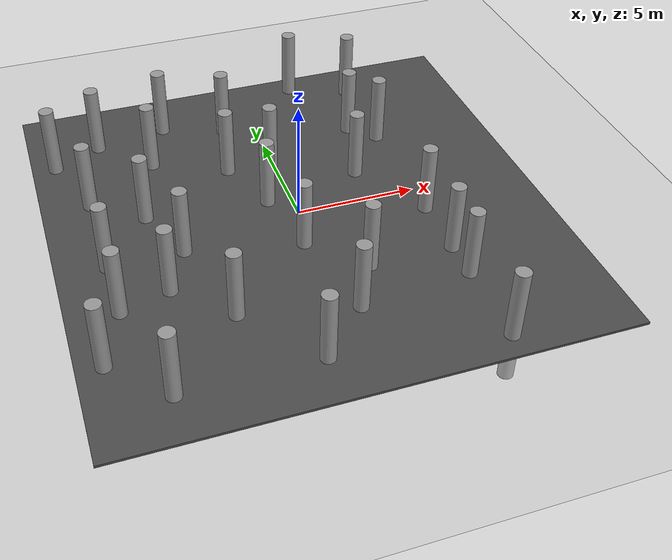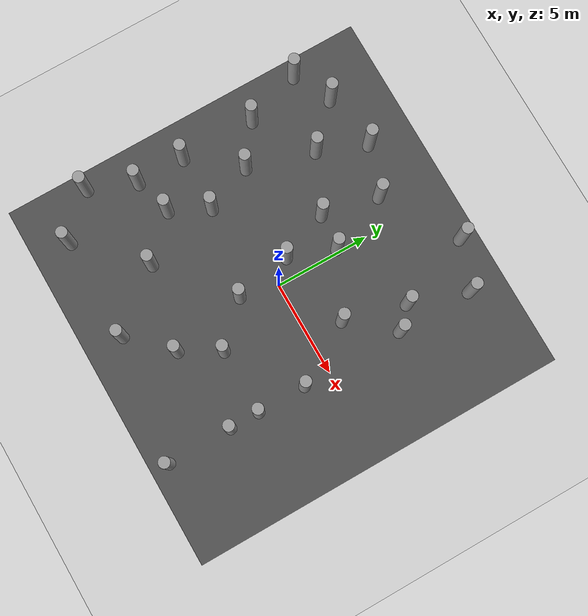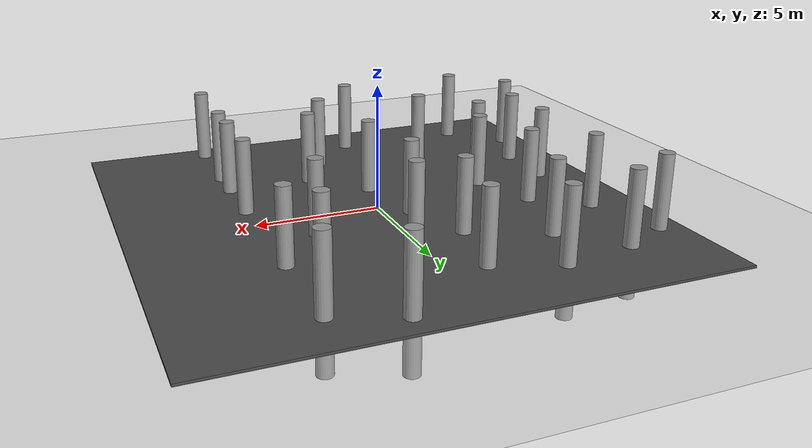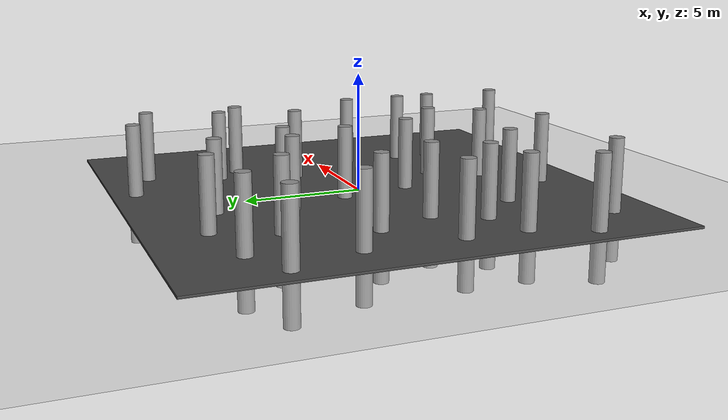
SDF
<sdf version="1.6">
 <world name="default">
  <light name="sun" type="directional">
   <pose>0 0 10 0 -0 0</pose>
   <diffuse>0.8 0.8 0.8 1</diffuse>
   <specular>0.2 0.2 0.2 1</specular>
   <attenuation>
    <range>1000</range>
    <constant>0.9</constant>
    <linear>0.01</linear>
    <quadratic>0.001</quadratic>
   </attenuation>
   <direction>-0.5 0.1 -0.9</direction>
  </light>
  <model name="ground_plane">
   <static>1</static>
   <link name="link">
    <collision name="collision">
     <geometry><plane><normal>0 0 1</normal><size>100 100</size></plane></geometry>
     <surface><friction><ode><mu>100</mu><mu2>50</mu2></ode></friction></surface>
    </collision>
    <visual name="visual">
     <cast_shadows>0</cast_shadows>
     <geometry><plane><normal>0 0 1</normal><size>100 100</size></plane></geometry>
     <material>
      <script><uri>file://media/materials/scripts/gazebo.material</uri><name>Gazebo/Grey</name></script>
     </material>
    </visual>
   </link>
  </model>
  <model name="asphalt_plane">
   <static>1</static>
   <link name="link">
    <collision name="collision"><geometry><box><size>20 20 0.1</size></box></geometry></collision>
    <visual name="visual">
     <cast_shadows>0</cast_shadows>
     <geometry><box><size>20 20 0.1</size></box></geometry>
     <material>
      <script>
       <uri>model://asphalt_plane/materials/scripts</uri>
       <uri>model://asphalt_plane/materials/textures</uri>
       <name>vrc/asphalt</name>
      </script>
     </material>
    </visual>
   </link>
  </model>
  <physics name="default_physics" default="0" type="ode">
   <ode>
    <solver>
     <type>quick</type>
     <iters>10</iters>
     <sor>1.3</sor>
     <use_dynamic_moi_rescaling>0</use_dynamic_moi_rescaling>
    </solver>
    <constraints>
     <cfm>0</cfm>
     <erp>0.2</erp>
     <contact_max_correcting_vel>100</contact_max_correcting_vel>
     <contact_surface_layer>0.001</contact_surface_layer>
    </constraints>
   </ode>
   <max_step_size>0.004</max_step_size>
   <real_time_factor>1</real_time_factor>
   <real_time_update_rate>250</real_time_update_rate>
  </physics>
  <gravity>0 0 -9.8066</gravity>
  <magnetic_field>6e-06 2.3e-05 -4.2e-05</magnetic_field>
  <atmosphere type="adiabatic"/>
  <scene><ambient>0.4 0.4 0.4 1</ambient><background>0.7 0.7 0.7 1</background><shadows>1</shadows></scene>
  <spherical_coordinates>
   <surface_model>EARTH_WGS84</surface_model>
   <latitude_deg>0</latitude_deg>
   <longitude_deg>0</longitude_deg>
   <elevation>0</elevation>
   <heading_deg>0</heading_deg>
  </spherical_coordinates>
  <model name="Untitled">
   <link name="link_1">
    <inertial>
     <mass>1</mass>
     <inertia><ixx>0.145833</ixx><ixy>0</ixy><ixz>0</ixz><iyy>0.145833</iyy><iyz>0</iyz><izz>0.125</izz></inertia>
    </inertial>
    <visual name="visual">
     <geometry><cylinder><radius>0.3</radius><length>5</length></cylinder></geometry>
     <material>
      <lighting>1</lighting>
      <script><uri>file://media/materials/scripts/gazebo.material</uri><name>Gazebo/Grey</name></script>
      <shader type="pixel"><normal_map>__default__</normal_map></shader>
      <ambient>0.3 0.3 0.3 1</ambient>
      <diffuse>0.7 0.7 0.7 1</diffuse>
      <specular>0.01 0.01 0.01 1</specular>
      <emissive>0 0 0 1</emissive>
     </material>
    </visual>
    <collision name="collision">
     <geometry><cylinder><radius>0.5</radius><length>1</length></cylinder></geometry>
     <surface>
      <friction>
       <ode><mu>1</mu><mu2>1</mu2><fdir1>0 0 0</fdir1><slip1>0</slip1><slip2>0</slip2></ode>
       <torsional>
        <coefficient>1</coefficient>
        <patch_radius>0</patch_radius>
        <surface_radius>0</surface_radius>
        <use_patch_radius>1</use_patch_radius>
        <ode><slip>0</slip></ode>
       </torsional>
      </friction>
      <bounce><restitution_coefficient>0</restitution_coefficient><threshold>1e+06</threshold></bounce>
      <contact>
       <collide_without_contact>0</collide_without_contact>
       <collide_without_contact_bitmask>1</collide_without_contact_bitmask>
       <collide_bitmask>1</collide_bitmask>
       <ode>
        <soft_cfm>0</soft_cfm>
        <soft_erp>0.2</soft_erp>
        <kp>1e+13</kp>
        <kd>1</kd>
        <max_vel>0.01</max_vel>
        <min_depth>0</min_depth>
       </ode>
       <bullet>
        <split_impulse>1</split_impulse>
        <split_impulse_penetration_threshold>-0.01</split_impulse_penetration_threshold>
        <soft_cfm>0</soft_cfm>
        <soft_erp>0.2</soft_erp>
        <kp>1e+13</kp>
        <kd>1</kd>
       </bullet>
      </contact>
     </surface>
    </collision>
   </link>
   <static>0</static>
   <pose>3.13644 1.77713 0.550029 -3e-06 -5.9e-05 0.014093</pose>
  </model>
  <model name="Untitled_clone">
   <link name="link_1">
    <inertial>
     <mass>1</mass>
     <inertia><ixx>0.145833</ixx><ixy>0</ixy><ixz>0</ixz><iyy>0.145833</iyy><iyz>0</iyz><izz>0.125</izz></inertia>
    </inertial>
    <visual name="visual">
     <geometry><cylinder><radius>0.3</radius><length>5</length></cylinder></geometry>
     <material>
      <lighting>1</lighting>
      <script><uri>file://media/materials/scripts/gazebo.material</uri><name>Gazebo/Grey</name></script>
      <shader type="pixel"><normal_map>__default__</normal_map></shader>
      <ambient>0.3 0.3 0.3 1</ambient>
      <diffuse>0.7 0.7 0.7 1</diffuse>
      <specular>0.01 0.01 0.01 1</specular>
      <emissive>0 0 0 1</emissive>
     </material>
    </visual>
    <collision name="collision">
     <geometry><cylinder><radius>0.5</radius><length>1</length></cylinder></geometry>
     <surface>
      <friction>
       <ode><mu>1</mu><mu2>1</mu2><fdir1>0 0 0</fdir1><slip1>0</slip1><slip2>0</slip2></ode>
       <torsional>
        <coefficient>1</coefficient>
        <patch_radius>0</patch_radius>
        <surface_radius>0</surface_radius>
        <use_patch_radius>1</use_patch_radius>
        <ode><slip>0</slip></ode>
       </torsional>
      </friction>
      <bounce><restitution_coefficient>0</restitution_coefficient><threshold>1e+06</threshold></bounce>
      <contact>
       <collide_without_contact>0</collide_without_contact>
       <collide_without_contact_bitmask>1</collide_without_contact_bitmask>
       <collide_bitmask>1</collide_bitmask>
       <ode>
        <soft_cfm>0</soft_cfm>
        <soft_erp>0.2</soft_erp>
        <kp>1e+13</kp>
        <kd>1</kd>
        <max_vel>0.01</max_vel>
        <min_depth>0</min_depth>
       </ode>
       <bullet>
        <split_impulse>1</split_impulse>
        <split_impulse_penetration_threshold>-0.01</split_impulse_penetration_threshold>
        <soft_cfm>0</soft_cfm>
        <soft_erp>0.2</soft_erp>
        <kp>1e+13</kp>
        <kd>1</kd>
       </bullet>
      </contact>
     </surface>
    </collision>
   </link>
   <static>0</static>
   <pose>-0.143533 3.39881 0.549816 -8e-05 6e-06 0.01388</pose>
  </model>
  <model name="Untitled_clone_0">
   <link name="link_1">
    <inertial>
     <mass>1</mass>
     <inertia><ixx>0.145833</ixx><ixy>0</ixy><ixz>0</ixz><iyy>0.145833</iyy><iyz>0</iyz><izz>0.125</izz></inertia>
    </inertial>
    <visual name="visual">
     <geometry><cylinder><radius>0.3</radius><length>5</length></cylinder></geometry>
     <material>
      <lighting>1</lighting>
      <script><uri>file://media/materials/scripts/gazebo.material</uri><name>Gazebo/Grey</name></script>
      <shader type="pixel"><normal_map>__default__</normal_map></shader>
      <ambient>0.3 0.3 0.3 1</ambient>
      <diffuse>0.7 0.7 0.7 1</diffuse>
      <specular>0.01 0.01 0.01 1</specular>
      <emissive>0 0 0 1</emissive>
     </material>
    </visual>
    <collision name="collision">
     <geometry><cylinder><radius>0.5</radius><length>1</length></cylinder></geometry>
     <surface>
      <friction>
       <ode><mu>1</mu><mu2>1</mu2><fdir1>0 0 0</fdir1><slip1>0</slip1><slip2>0</slip2></ode>
       <torsional>
        <coefficient>1</coefficient>
        <patch_radius>0</patch_radius>
        <surface_radius>0</surface_radius>
        <use_patch_radius>1</use_patch_radius>
        <ode><slip>0</slip></ode>
       </torsional>
      </friction>
      <bounce><restitution_coefficient>0</restitution_coefficient><threshold>1e+06</threshold></bounce>
      <contact>
       <collide_without_contact>0</collide_without_contact>
       <collide_without_contact_bitmask>1</collide_without_contact_bitmask>
       <collide_bitmask>1</collide_bitmask>
       <ode>
        <soft_cfm>0</soft_cfm>
        <soft_erp>0.2</soft_erp>
        <kp>1e+13</kp>
        <kd>1</kd>
        <max_vel>0.01</max_vel>
        <min_depth>0</min_depth>
       </ode>
       <bullet>
        <split_impulse>1</split_impulse>
        <split_impulse_penetration_threshold>-0.01</split_impulse_penetration_threshold>
        <soft_cfm>0</soft_cfm>
        <soft_erp>0.2</soft_erp>
        <kp>1e+13</kp>
        <kd>1</kd>
       </bullet>
      </contact>
     </surface>
    </collision>
   </link>
   <static>0</static>
   <pose>3.99979 4.99944 0.549953 1.7e-05 9.6e-05 0.014262</pose>
  </model>
  <model name="Untitled_clone_1">
   <link name="link_1">
    <inertial>
     <mass>1</mass>
     <inertia><ixx>0.145833</ixx><ixy>0</ixy><ixz>0</ixz><iyy>0.145833</iyy><iyz>0</iyz><izz>0.125</izz></inertia>
    </inertial>
    <visual name="visual">
     <geometry><cylinder><radius>0.3</radius><length>5</length></cylinder></geometry>
     <material>
      <lighting>1</lighting>
      <script><uri>file://media/materials/scripts/gazebo.material</uri><name>Gazebo/Grey</name></script>
      <shader type="pixel"><normal_map>__default__</normal_map></shader>
      <ambient>0.3 0.3 0.3 1</ambient>
      <diffuse>0.7 0.7 0.7 1</diffuse>
      <specular>0.01 0.01 0.01 1</specular>
      <emissive>0 0 0 1</emissive>
     </material>
    </visual>
    <collision name="collision">
     <geometry><cylinder><radius>0.5</radius><length>1</length></cylinder></geometry>
     <surface>
      <friction>
       <ode><mu>1</mu><mu2>1</mu2><fdir1>0 0 0</fdir1><slip1>0</slip1><slip2>0</slip2></ode>
       <torsional>
        <coefficient>1</coefficient>
        <patch_radius>0</patch_radius>
        <surface_radius>0</surface_radius>
        <use_patch_radius>1</use_patch_radius>
        <ode><slip>0</slip></ode>
       </torsional>
      </friction>
      <bounce><restitution_coefficient>0</restitution_coefficient><threshold>1e+06</threshold></bounce>
      <contact>
       <collide_without_contact>0</collide_without_contact>
       <collide_without_contact_bitmask>1</collide_without_contact_bitmask>
       <collide_bitmask>1</collide_bitmask>
       <ode>
        <soft_cfm>0</soft_cfm>
        <soft_erp>0.2</soft_erp>
        <kp>1e+13</kp>
        <kd>1</kd>
        <max_vel>0.01</max_vel>
        <min_depth>0</min_depth>
       </ode>
       <bullet>
        <split_impulse>1</split_impulse>
        <split_impulse_penetration_threshold>-0.01</split_impulse_penetration_threshold>
        <soft_cfm>0</soft_cfm>
        <soft_erp>0.2</soft_erp>
        <kp>1e+13</kp>
        <kd>1</kd>
       </bullet>
      </contact>
     </surface>
    </collision>
   </link>
   <static>0</static>
   <pose>4.99957 3.9995 0.549984 4e-06 3.1e-05 0.013668</pose>
  </model>
  <model name="Untitled_clone_2">
   <link name="link_1">
    <inertial>
     <mass>1</mass>
     <inertia><ixx>0.145833</ixx><ixy>0</ixy><ixz>0</ixz><iyy>0.145833</iyy><iyz>0</iyz><izz>0.125</izz></inertia>
    </inertial>
    <visual name="visual">
     <geometry><cylinder><radius>0.3</radius><length>5</length></cylinder></geometry>
     <material>
      <lighting>1</lighting>
      <script><uri>file://media/materials/scripts/gazebo.material</uri><name>Gazebo/Grey</name></script>
      <shader type="pixel"><normal_map>__default__</normal_map></shader>
      <ambient>0.3 0.3 0.3 1</ambient>
      <diffuse>0.7 0.7 0.7 1</diffuse>
      <specular>0.01 0.01 0.01 1</specular>
      <emissive>0 0 0 1</emissive>
     </material>
    </visual>
    <collision name="collision">
     <geometry><cylinder><radius>0.5</radius><length>1</length></cylinder></geometry>
     <surface>
      <friction>
       <ode><mu>1</mu><mu2>1</mu2><fdir1>0 0 0</fdir1><slip1>0</slip1><slip2>0</slip2></ode>
       <torsional>
        <coefficient>1</coefficient>
        <patch_radius>0</patch_radius>
        <surface_radius>0</surface_radius>
        <use_patch_radius>1</use_patch_radius>
        <ode><slip>0</slip></ode>
       </torsional>
      </friction>
      <bounce><restitution_coefficient>0</restitution_coefficient><threshold>1e+06</threshold></bounce>
      <contact>
       <collide_without_contact>0</collide_without_contact>
       <collide_without_contact_bitmask>1</collide_without_contact_bitmask>
       <collide_bitmask>1</collide_bitmask>
       <ode>
        <soft_cfm>0</soft_cfm>
        <soft_erp>0.2</soft_erp>
        <kp>1e+13</kp>
        <kd>1</kd>
        <max_vel>0.01</max_vel>
        <min_depth>0</min_depth>
       </ode>
       <bullet>
        <split_impulse>1</split_impulse>
        <split_impulse_penetration_threshold>-0.01</split_impulse_penetration_threshold>
        <soft_cfm>0</soft_cfm>
        <soft_erp>0.2</soft_erp>
        <kp>1e+13</kp>
        <kd>1</kd>
       </bullet>
      </contact>
     </surface>
    </collision>
   </link>
   <static>0</static>
   <pose>4.99925 -1.41702 0.549996 1e-06 8e-06 0.013483</pose>
  </model>
  <model name="Untitled_clone_3">
   <link name="link_1">
    <inertial>
     <mass>1</mass>
     <inertia><ixx>0.145833</ixx><ixy>0</ixy><ixz>0</ixz><iyy>0.145833</iyy><iyz>0</iyz><izz>0.125</izz></inertia>
    </inertial>
    <visual name="visual">
     <geometry><cylinder><radius>0.3</radius><length>5</length></cylinder></geometry>
     <material>
      <lighting>1</lighting>
      <script><uri>file://media/materials/scripts/gazebo.material</uri><name>Gazebo/Grey</name></script>
      <shader type="pixel"><normal_map>__default__</normal_map></shader>
      <ambient>0.3 0.3 0.3 1</ambient>
      <diffuse>0.7 0.7 0.7 1</diffuse>
      <specular>0.01 0.01 0.01 1</specular>
      <emissive>0 0 0 1</emissive>
     </material>
    </visual>
    <collision name="collision">
     <geometry><cylinder><radius>0.5</radius><length>1</length></cylinder></geometry>
     <surface>
      <friction>
       <ode><mu>1</mu><mu2>1</mu2><fdir1>0 0 0</fdir1><slip1>0</slip1><slip2>0</slip2></ode>
       <torsional>
        <coefficient>1</coefficient>
        <patch_radius>0</patch_radius>
        <surface_radius>0</surface_radius>
        <use_patch_radius>1</use_patch_radius>
        <ode><slip>0</slip></ode>
       </torsional>
      </friction>
      <bounce><restitution_coefficient>0</restitution_coefficient><threshold>1e+06</threshold></bounce>
      <contact>
       <collide_without_contact>0</collide_without_contact>
       <collide_without_contact_bitmask>1</collide_without_contact_bitmask>
       <collide_bitmask>1</collide_bitmask>
       <ode>
        <soft_cfm>0</soft_cfm>
        <soft_erp>0.2</soft_erp>
        <kp>1e+13</kp>
        <kd>1</kd>
        <max_vel>0.01</max_vel>
        <min_depth>0</min_depth>
       </ode>
       <bullet>
        <split_impulse>1</split_impulse>
        <split_impulse_penetration_threshold>-0.01</split_impulse_penetration_threshold>
        <soft_cfm>0</soft_cfm>
        <soft_erp>0.2</soft_erp>
        <kp>1e+13</kp>
        <kd>1</kd>
       </bullet>
      </contact>
     </surface>
    </collision>
   </link>
   <static>0</static>
   <pose>-0.40703 -2.00042 0.549974 -3e-06 -6.9e-05 0.013907</pose>
  </model>
  <model name="Untitled_clone_4">
   <link name="link_1">
    <inertial>
     <mass>1</mass>
     <inertia><ixx>0.145833</ixx><ixy>0</ixy><ixz>0</ixz><iyy>0.145833</iyy><iyz>0</iyz><izz>0.125</izz></inertia>
    </inertial>
    <visual name="visual">
     <geometry><cylinder><radius>0.3</radius><length>5</length></cylinder></geometry>
     <material>
      <lighting>1</lighting>
      <script><uri>file://media/materials/scripts/gazebo.material</uri><name>Gazebo/Grey</name></script>
      <shader type="pixel"><normal_map>__default__</normal_map></shader>
      <ambient>0.3 0.3 0.3 1</ambient>
      <diffuse>0.7 0.7 0.7 1</diffuse>
      <specular>0.01 0.01 0.01 1</specular>
      <emissive>0 0 0 1</emissive>
     </material>
    </visual>
    <collision name="collision">
     <geometry><cylinder><radius>0.5</radius><length>1</length></cylinder></geometry>
     <surface>
      <friction>
       <ode><mu>1</mu><mu2>1</mu2><fdir1>0 0 0</fdir1><slip1>0</slip1><slip2>0</slip2></ode>
       <torsional>
        <coefficient>1</coefficient>
        <patch_radius>0</patch_radius>
        <surface_radius>0</surface_radius>
        <use_patch_radius>1</use_patch_radius>
        <ode><slip>0</slip></ode>
       </torsional>
      </friction>
      <bounce><restitution_coefficient>0</restitution_coefficient><threshold>1e+06</threshold></bounce>
      <contact>
       <collide_without_contact>0</collide_without_contact>
       <collide_without_contact_bitmask>1</collide_without_contact_bitmask>
       <collide_bitmask>1</collide_bitmask>
       <ode>
        <soft_cfm>0</soft_cfm>
        <soft_erp>0.2</soft_erp>
        <kp>1e+13</kp>
        <kd>1</kd>
        <max_vel>0.01</max_vel>
        <min_depth>0</min_depth>
       </ode>
       <bullet>
        <split_impulse>1</split_impulse>
        <split_impulse_penetration_threshold>-0.01</split_impulse_penetration_threshold>
        <soft_cfm>0</soft_cfm>
        <soft_erp>0.2</soft_erp>
        <kp>1e+13</kp>
        <kd>1</kd>
       </bullet>
      </contact>
     </surface>
    </collision>
   </link>
   <static>0</static>
   <pose>-4.00047 -5.00044 0.550034 -1.2e-05 -6.8e-05 0.013936</pose>
  </model>
  <model name="Untitled_clone_5">
   <link name="link_1">
    <inertial>
     <mass>1</mass>
     <inertia><ixx>0.145833</ixx><ixy>0</ixy><ixz>0</ixz><iyy>0.145833</iyy><iyz>0</iyz><izz>0.125</izz></inertia>
    </inertial>
    <visual name="visual">
     <geometry><cylinder><radius>0.3</radius><length>5</length></cylinder></geometry>
     <material>
      <lighting>1</lighting>
      <script><uri>file://media/materials/scripts/gazebo.material</uri><name>Gazebo/Grey</name></script>
      <shader type="pixel"><normal_map>__default__</normal_map></shader>
      <ambient>0.3 0.3 0.3 1</ambient>
      <diffuse>0.7 0.7 0.7 1</diffuse>
      <specular>0.01 0.01 0.01 1</specular>
      <emissive>0 0 0 1</emissive>
     </material>
    </visual>
    <collision name="collision">
     <geometry><cylinder><radius>0.5</radius><length>1</length></cylinder></geometry>
     <surface>
      <friction>
       <ode><mu>1</mu><mu2>1</mu2><fdir1>0 0 0</fdir1><slip1>0</slip1><slip2>0</slip2></ode>
       <torsional>
        <coefficient>1</coefficient>
        <patch_radius>0</patch_radius>
        <surface_radius>0</surface_radius>
        <use_patch_radius>1</use_patch_radius>
        <ode><slip>0</slip></ode>
       </torsional>
      </friction>
      <bounce><restitution_coefficient>0</restitution_coefficient><threshold>1e+06</threshold></bounce>
      <contact>
       <collide_without_contact>0</collide_without_contact>
       <collide_without_contact_bitmask>1</collide_without_contact_bitmask>
       <collide_bitmask>1</collide_bitmask>
       <ode>
        <soft_cfm>0</soft_cfm>
        <soft_erp>0.2</soft_erp>
        <kp>1e+13</kp>
        <kd>1</kd>
        <max_vel>0.01</max_vel>
        <min_depth>0</min_depth>
       </ode>
       <bullet>
        <split_impulse>1</split_impulse>
        <split_impulse_penetration_threshold>-0.01</split_impulse_penetration_threshold>
        <soft_cfm>0</soft_cfm>
        <soft_erp>0.2</soft_erp>
        <kp>1e+13</kp>
        <kd>1</kd>
       </bullet>
      </contact>
     </surface>
    </collision>
   </link>
   <static>0</static>
   <pose>-5.99993 -3.00017 0.549912 -5.3e-05 -2.4e-05 0.014778</pose>
  </model>
  <model name="Untitled_clone_6">
   <link name="link_1">
    <inertial>
     <mass>1</mass>
     <inertia><ixx>0.145833</ixx><ixy>0</ixy><ixz>0</ixz><iyy>0.145833</iyy><iyz>0</iyz><izz>0.125</izz></inertia>
    </inertial>
    <visual name="visual">
     <geometry><cylinder><radius>0.3</radius><length>5</length></cylinder></geometry>
     <material>
      <lighting>1</lighting>
      <script><uri>file://media/materials/scripts/gazebo.material</uri><name>Gazebo/Grey</name></script>
      <shader type="pixel"><normal_map>__default__</normal_map></shader>
      <ambient>0.3 0.3 0.3 1</ambient>
      <diffuse>0.7 0.7 0.7 1</diffuse>
      <specular>0.01 0.01 0.01 1</specular>
      <emissive>0 0 0 1</emissive>
     </material>
    </visual>
    <collision name="collision">
     <geometry><cylinder><radius>0.5</radius><length>1</length></cylinder></geometry>
     <surface>
      <friction>
       <ode><mu>1</mu><mu2>1</mu2><fdir1>0 0 0</fdir1><slip1>0</slip1><slip2>0</slip2></ode>
       <torsional>
        <coefficient>1</coefficient>
        <patch_radius>0</patch_radius>
        <surface_radius>0</surface_radius>
        <use_patch_radius>1</use_patch_radius>
        <ode><slip>0</slip></ode>
       </torsional>
      </friction>
      <bounce><restitution_coefficient>0</restitution_coefficient><threshold>1e+06</threshold></bounce>
      <contact>
       <collide_without_contact>0</collide_without_contact>
       <collide_without_contact_bitmask>1</collide_without_contact_bitmask>
       <collide_bitmask>1</collide_bitmask>
       <ode>
        <soft_cfm>0</soft_cfm>
        <soft_erp>0.2</soft_erp>
        <kp>1e+13</kp>
        <kd>1</kd>
        <max_vel>0.01</max_vel>
        <min_depth>0</min_depth>
       </ode>
       <bullet>
        <split_impulse>1</split_impulse>
        <split_impulse_penetration_threshold>-0.01</split_impulse_penetration_threshold>
        <soft_cfm>0</soft_cfm>
        <soft_erp>0.2</soft_erp>
        <kp>1e+13</kp>
        <kd>1</kd>
       </bullet>
      </contact>
     </surface>
    </collision>
   </link>
   <static>0</static>
   <pose>-6.00035 1.50269 0.550023 -1.4e-05 -4.5e-05 0.013903</pose>
  </model>
  <model name="Untitled_clone_7">
   <link name="link_1">
    <inertial>
     <mass>1</mass>
     <inertia><ixx>0.145833</ixx><ixy>0</ixy><ixz>0</ixz><iyy>0.145833</iyy><iyz>0</iyz><izz>0.125</izz></inertia>
    </inertial>
    <visual name="visual">
     <geometry><cylinder><radius>0.3</radius><length>5</length></cylinder></geometry>
     <material>
      <lighting>1</lighting>
      <script><uri>file://media/materials/scripts/gazebo.material</uri><name>Gazebo/Grey</name></script>
      <shader type="pixel"><normal_map>__default__</normal_map></shader>
      <ambient>0.3 0.3 0.3 1</ambient>
      <diffuse>0.7 0.7 0.7 1</diffuse>
      <specular>0.01 0.01 0.01 1</specular>
      <emissive>0 0 0 1</emissive>
     </material>
    </visual>
    <collision name="collision">
     <geometry><cylinder><radius>0.5</radius><length>1</length></cylinder></geometry>
     <surface>
      <friction>
       <ode><mu>1</mu><mu2>1</mu2><fdir1>0 0 0</fdir1><slip1>0</slip1><slip2>0</slip2></ode>
       <torsional>
        <coefficient>1</coefficient>
        <patch_radius>0</patch_radius>
        <surface_radius>0</surface_radius>
        <use_patch_radius>1</use_patch_radius>
        <ode><slip>0</slip></ode>
       </torsional>
      </friction>
      <bounce><restitution_coefficient>0</restitution_coefficient><threshold>1e+06</threshold></bounce>
      <contact>
       <collide_without_contact>0</collide_without_contact>
       <collide_without_contact_bitmask>1</collide_without_contact_bitmask>
       <collide_bitmask>1</collide_bitmask>
       <ode>
        <soft_cfm>0</soft_cfm>
        <soft_erp>0.2</soft_erp>
        <kp>1e+13</kp>
        <kd>1</kd>
        <max_vel>0.01</max_vel>
        <min_depth>0</min_depth>
       </ode>
       <bullet>
        <split_impulse>1</split_impulse>
        <split_impulse_penetration_threshold>-0.01</split_impulse_penetration_threshold>
        <soft_cfm>0</soft_cfm>
        <soft_erp>0.2</soft_erp>
        <kp>1e+13</kp>
        <kd>1</kd>
       </bullet>
      </contact>
     </surface>
    </collision>
   </link>
   <static>0</static>
   <pose>-5.00031 4.99965 0.549987 -1e-06 2.7e-05 0.013865</pose>
  </model>
  <model name="Untitled_clone_8">
   <link name="link_1">
    <inertial>
     <mass>1</mass>
     <inertia><ixx>0.145833</ixx><ixy>0</ixy><ixz>0</ixz><iyy>0.145833</iyy><iyz>0</iyz><izz>0.125</izz></inertia>
    </inertial>
    <visual name="visual">
     <geometry><cylinder><radius>0.3</radius><length>5</length></cylinder></geometry>
     <material>
      <lighting>1</lighting>
      <script><uri>file://media/materials/scripts/gazebo.material</uri><name>Gazebo/Grey</name></script>
      <shader type="pixel"><normal_map>__default__</normal_map></shader>
      <ambient>0.3 0.3 0.3 1</ambient>
      <diffuse>0.7 0.7 0.7 1</diffuse>
      <specular>0.01 0.01 0.01 1</specular>
      <emissive>0 0 0 1</emissive>
     </material>
    </visual>
    <collision name="collision">
     <geometry><cylinder><radius>0.5</radius><length>1</length></cylinder></geometry>
     <surface>
      <friction>
       <ode><mu>1</mu><mu2>1</mu2><fdir1>0 0 0</fdir1><slip1>0</slip1><slip2>0</slip2></ode>
       <torsional>
        <coefficient>1</coefficient>
        <patch_radius>0</patch_radius>
        <surface_radius>0</surface_radius>
        <use_patch_radius>1</use_patch_radius>
        <ode><slip>0</slip></ode>
       </torsional>
      </friction>
      <bounce><restitution_coefficient>0</restitution_coefficient><threshold>1e+06</threshold></bounce>
      <contact>
       <collide_without_contact>0</collide_without_contact>
       <collide_without_contact_bitmask>1</collide_without_contact_bitmask>
       <collide_bitmask>1</collide_bitmask>
       <ode>
        <soft_cfm>0</soft_cfm>
        <soft_erp>0.2</soft_erp>
        <kp>1e+13</kp>
        <kd>1</kd>
        <max_vel>0.01</max_vel>
        <min_depth>0</min_depth>
       </ode>
       <bullet>
        <split_impulse>1</split_impulse>
        <split_impulse_penetration_threshold>-0.01</split_impulse_penetration_threshold>
        <soft_cfm>0</soft_cfm>
        <soft_erp>0.2</soft_erp>
        <kp>1e+13</kp>
        <kd>1</kd>
       </bullet>
      </contact>
     </surface>
    </collision>
   </link>
   <static>0</static>
   <pose>-1.40123 6.57859 0.550014 1e-06 3.4e-05 0.013762</pose>
  </model>
  <model name="Untitled_clone_9">
   <link name="link_1">
    <inertial>
     <mass>1</mass>
     <inertia><ixx>0.145833</ixx><ixy>0</ixy><ixz>0</ixz><iyy>0.145833</iyy><iyz>0</iyz><izz>0.125</izz></inertia>
    </inertial>
    <visual name="visual">
     <geometry><cylinder><radius>0.3</radius><length>5</length></cylinder></geometry>
     <material>
      <lighting>1</lighting>
      <script><uri>file://media/materials/scripts/gazebo.material</uri><name>Gazebo/Grey</name></script>
      <shader type="pixel"><normal_map>__default__</normal_map></shader>
      <ambient>0.3 0.3 0.3 1</ambient>
      <diffuse>0.7 0.7 0.7 1</diffuse>
      <specular>0.01 0.01 0.01 1</specular>
      <emissive>0 0 0 1</emissive>
     </material>
    </visual>
    <collision name="collision">
     <geometry><cylinder><radius>0.5</radius><length>1</length></cylinder></geometry>
     <surface>
      <friction>
       <ode><mu>1</mu><mu2>1</mu2><fdir1>0 0 0</fdir1><slip1>0</slip1><slip2>0</slip2></ode>
       <torsional>
        <coefficient>1</coefficient>
        <patch_radius>0</patch_radius>
        <surface_radius>0</surface_radius>
        <use_patch_radius>1</use_patch_radius>
        <ode><slip>0</slip></ode>
       </torsional>
      </friction>
      <bounce><restitution_coefficient>0</restitution_coefficient><threshold>1e+06</threshold></bounce>
      <contact>
       <collide_without_contact>0</collide_without_contact>
       <collide_without_contact_bitmask>1</collide_without_contact_bitmask>
       <collide_bitmask>1</collide_bitmask>
       <ode>
        <soft_cfm>0</soft_cfm>
        <soft_erp>0.2</soft_erp>
        <kp>1e+13</kp>
        <kd>1</kd>
        <max_vel>0.01</max_vel>
        <min_depth>0</min_depth>
       </ode>
       <bullet>
        <split_impulse>1</split_impulse>
        <split_impulse_penetration_threshold>-0.01</split_impulse_penetration_threshold>
        <soft_cfm>0</soft_cfm>
        <soft_erp>0.2</soft_erp>
        <kp>1e+13</kp>
        <kd>1</kd>
       </bullet>
      </contact>
     </surface>
    </collision>
   </link>
   <static>0</static>
   <pose>-2.00041 3.59288 0.549903 -2.9e-05 -2.4e-05 0.013803</pose>
  </model>
  <model name="Untitled_clone_10">
   <link name="link_1">
    <inertial>
     <mass>1</mass>
     <inertia><ixx>0.145833</ixx><ixy>0</ixy><ixz>0</ixz><iyy>0.145833</iyy><iyz>0</iyz><izz>0.125</izz></inertia>
    </inertial>
    <visual name="visual">
     <geometry><cylinder><radius>0.3</radius><length>5</length></cylinder></geometry>
     <material>
      <lighting>1</lighting>
      <script><uri>file://media/materials/scripts/gazebo.material</uri><name>Gazebo/Grey</name></script>
      <shader type="pixel"><normal_map>__default__</normal_map></shader>
      <ambient>0.3 0.3 0.3 1</ambient>
      <diffuse>0.7 0.7 0.7 1</diffuse>
      <specular>0.01 0.01 0.01 1</specular>
      <emissive>0 0 0 1</emissive>
     </material>
    </visual>
    <collision name="collision">
     <geometry><cylinder><radius>0.5</radius><length>1</length></cylinder></geometry>
     <surface>
      <friction>
       <ode><mu>1</mu><mu2>1</mu2><fdir1>0 0 0</fdir1><slip1>0</slip1><slip2>0</slip2></ode>
       <torsional>
        <coefficient>1</coefficient>
        <patch_radius>0</patch_radius>
        <surface_radius>0</surface_radius>
        <use_patch_radius>1</use_patch_radius>
        <ode><slip>0</slip></ode>
       </torsional>
      </friction>
      <bounce><restitution_coefficient>0</restitution_coefficient><threshold>1e+06</threshold></bounce>
      <contact>
       <collide_without_contact>0</collide_without_contact>
       <collide_without_contact_bitmask>1</collide_without_contact_bitmask>
       <collide_bitmask>1</collide_bitmask>
       <ode>
        <soft_cfm>0</soft_cfm>
        <soft_erp>0.2</soft_erp>
        <kp>1e+13</kp>
        <kd>1</kd>
        <max_vel>0.01</max_vel>
        <min_depth>0</min_depth>
       </ode>
       <bullet>
        <split_impulse>1</split_impulse>
        <split_impulse_penetration_threshold>-0.01</split_impulse_penetration_threshold>
        <soft_cfm>0</soft_cfm>
        <soft_erp>0.2</soft_erp>
        <kp>1e+13</kp>
        <kd>1</kd>
       </bullet>
      </contact>
     </surface>
    </collision>
   </link>
   <static>0</static>
   <pose>-5.00041 -1.00041 0.550031 -1.1e-05 -6.2e-05 0.013816</pose>
  </model>
  <model name="Untitled_clone_11">
   <link name="link_1">
    <inertial>
     <mass>1</mass>
     <inertia><ixx>0.145833</ixx><ixy>0</ixy><ixz>0</ixz><iyy>0.145833</iyy><iyz>0</iyz><izz>0.125</izz></inertia>
    </inertial>
    <visual name="visual">
     <geometry><cylinder><radius>0.3</radius><length>5</length></cylinder></geometry>
     <material>
      <lighting>1</lighting>
      <script><uri>file://media/materials/scripts/gazebo.material</uri><name>Gazebo/Grey</name></script>
      <shader type="pixel"><normal_map>__default__</normal_map></shader>
      <ambient>0.3 0.3 0.3 1</ambient>
      <diffuse>0.7 0.7 0.7 1</diffuse>
      <specular>0.01 0.01 0.01 1</specular>
      <emissive>0 0 0 1</emissive>
     </material>
    </visual>
    <collision name="collision">
     <geometry><cylinder><radius>0.5</radius><length>1</length></cylinder></geometry>
     <surface>
      <friction>
       <ode><mu>1</mu><mu2>1</mu2><fdir1>0 0 0</fdir1><slip1>0</slip1><slip2>0</slip2></ode>
       <torsional>
        <coefficient>1</coefficient>
        <patch_radius>0</patch_radius>
        <surface_radius>0</surface_radius>
        <use_patch_radius>1</use_patch_radius>
        <ode><slip>0</slip></ode>
       </torsional>
      </friction>
      <bounce><restitution_coefficient>0</restitution_coefficient><threshold>1e+06</threshold></bounce>
      <contact>
       <collide_without_contact>0</collide_without_contact>
       <collide_without_contact_bitmask>1</collide_without_contact_bitmask>
       <collide_bitmask>1</collide_bitmask>
       <ode>
        <soft_cfm>0</soft_cfm>
        <soft_erp>0.2</soft_erp>
        <kp>1e+13</kp>
        <kd>1</kd>
        <max_vel>0.01</max_vel>
        <min_depth>0</min_depth>
       </ode>
       <bullet>
        <split_impulse>1</split_impulse>
        <split_impulse_penetration_threshold>-0.01</split_impulse_penetration_threshold>
        <soft_cfm>0</soft_cfm>
        <soft_erp>0.2</soft_erp>
        <kp>1e+13</kp>
        <kd>1</kd>
       </bullet>
      </contact>
     </surface>
    </collision>
   </link>
   <static>0</static>
   <pose>0.432623 -6.0002 0.549958 1e-05 8.4e-05 0.013612</pose>
  </model>
  <model name="Untitled_clone_12">
   <link name="link_1">
    <inertial>
     <mass>1</mass>
     <inertia><ixx>0.145833</ixx><ixy>0</ixy><ixz>0</ixz><iyy>0.145833</iyy><iyz>0</iyz><izz>0.125</izz></inertia>
    </inertial>
    <visual name="visual">
     <geometry><cylinder><radius>0.3</radius><length>5</length></cylinder></geometry>
     <material>
      <lighting>1</lighting>
      <script><uri>file://media/materials/scripts/gazebo.material</uri><name>Gazebo/Grey</name></script>
      <shader type="pixel"><normal_map>__default__</normal_map></shader>
      <ambient>0.3 0.3 0.3 1</ambient>
      <diffuse>0.7 0.7 0.7 1</diffuse>
      <specular>0.01 0.01 0.01 1</specular>
      <emissive>0 0 0 1</emissive>
     </material>
    </visual>
    <collision name="collision">
     <geometry><cylinder><radius>0.5</radius><length>1</length></cylinder></geometry>
     <surface>
      <friction>
       <ode><mu>1</mu><mu2>1</mu2><fdir1>0 0 0</fdir1><slip1>0</slip1><slip2>0</slip2></ode>
       <torsional>
        <coefficient>1</coefficient>
        <patch_radius>0</patch_radius>
        <surface_radius>0</surface_radius>
        <use_patch_radius>1</use_patch_radius>
        <ode><slip>0</slip></ode>
       </torsional>
      </friction>
      <bounce><restitution_coefficient>0</restitution_coefficient><threshold>1e+06</threshold></bounce>
      <contact>
       <collide_without_contact>0</collide_without_contact>
       <collide_without_contact_bitmask>1</collide_without_contact_bitmask>
       <collide_bitmask>1</collide_bitmask>
       <ode>
        <soft_cfm>0</soft_cfm>
        <soft_erp>0.2</soft_erp>
        <kp>1e+13</kp>
        <kd>1</kd>
        <max_vel>0.01</max_vel>
        <min_depth>0</min_depth>
       </ode>
       <bullet>
        <split_impulse>1</split_impulse>
        <split_impulse_penetration_threshold>-0.01</split_impulse_penetration_threshold>
        <soft_cfm>0</soft_cfm>
        <soft_erp>0.2</soft_erp>
        <kp>1e+13</kp>
        <kd>1</kd>
       </bullet>
      </contact>
     </surface>
    </collision>
   </link>
   <static>0</static>
   <pose>4.99941 -5.57312 0.549886 -2e-06 -4e-06 0.013416</pose>
  </model>
  <model name="Untitled_clone_13">
   <link name="link_1">
    <inertial>
     <mass>1</mass>
     <inertia><ixx>0.145833</ixx><ixy>0</ixy><ixz>0</ixz><iyy>0.145833</iyy><iyz>0</iyz><izz>0.125</izz></inertia>
    </inertial>
    <visual name="visual">
     <geometry><cylinder><radius>0.3</radius><length>5</length></cylinder></geometry>
     <material>
      <lighting>1</lighting>
      <script><uri>file://media/materials/scripts/gazebo.material</uri><name>Gazebo/Grey</name></script>
      <shader type="pixel"><normal_map>__default__</normal_map></shader>
      <ambient>0.3 0.3 0.3 1</ambient>
      <diffuse>0.7 0.7 0.7 1</diffuse>
      <specular>0.01 0.01 0.01 1</specular>
      <emissive>0 0 0 1</emissive>
     </material>
    </visual>
    <collision name="collision">
     <geometry><cylinder><radius>0.5</radius><length>1</length></cylinder></geometry>
     <surface>
      <friction>
       <ode><mu>1</mu><mu2>1</mu2><fdir1>0 0 0</fdir1><slip1>0</slip1><slip2>0</slip2></ode>
       <torsional>
        <coefficient>1</coefficient>
        <patch_radius>0</patch_radius>
        <surface_radius>0</surface_radius>
        <use_patch_radius>1</use_patch_radius>
        <ode><slip>0</slip></ode>
       </torsional>
      </friction>
      <bounce><restitution_coefficient>0</restitution_coefficient><threshold>1e+06</threshold></bounce>
      <contact>
       <collide_without_contact>0</collide_without_contact>
       <collide_without_contact_bitmask>1</collide_without_contact_bitmask>
       <collide_bitmask>1</collide_bitmask>
       <ode>
        <soft_cfm>0</soft_cfm>
        <soft_erp>0.2</soft_erp>
        <kp>1e+13</kp>
        <kd>1</kd>
        <max_vel>0.01</max_vel>
        <min_depth>0</min_depth>
       </ode>
       <bullet>
        <split_impulse>1</split_impulse>
        <split_impulse_penetration_threshold>-0.01</split_impulse_penetration_threshold>
        <soft_cfm>0</soft_cfm>
        <soft_erp>0.2</soft_erp>
        <kp>1e+13</kp>
        <kd>1</kd>
       </bullet>
      </contact>
     </surface>
    </collision>
   </link>
   <static>0</static>
   <pose>4.99936 -4.00021 0.550034 -6.5e-05 -2.2e-05 0.013137</pose>
  </model>
  <model name="Untitled_clone_14">
   <link name="link_1">
    <inertial>
     <mass>1</mass>
     <inertia><ixx>0.145833</ixx><ixy>0</ixy><ixz>0</ixz><iyy>0.145833</iyy><iyz>0</iyz><izz>0.125</izz></inertia>
    </inertial>
    <visual name="visual">
     <geometry><cylinder><radius>0.3</radius><length>5</length></cylinder></geometry>
     <material>
      <lighting>1</lighting>
      <script><uri>file://media/materials/scripts/gazebo.material</uri><name>Gazebo/Grey</name></script>
      <shader type="pixel"><normal_map>__default__</normal_map></shader>
      <ambient>0.3 0.3 0.3 1</ambient>
      <diffuse>0.7 0.7 0.7 1</diffuse>
      <specular>0.01 0.01 0.01 1</specular>
      <emissive>0 0 0 1</emissive>
     </material>
    </visual>
    <collision name="collision">
     <geometry><cylinder><radius>0.5</radius><length>1</length></cylinder></geometry>
     <surface>
      <friction>
       <ode><mu>1</mu><mu2>1</mu2><fdir1>0 0 0</fdir1><slip1>0</slip1><slip2>0</slip2></ode>
       <torsional>
        <coefficient>1</coefficient>
        <patch_radius>0</patch_radius>
        <surface_radius>0</surface_radius>
        <use_patch_radius>1</use_patch_radius>
        <ode><slip>0</slip></ode>
       </torsional>
      </friction>
      <bounce><restitution_coefficient>0</restitution_coefficient><threshold>1e+06</threshold></bounce>
      <contact>
       <collide_without_contact>0</collide_without_contact>
       <collide_without_contact_bitmask>1</collide_without_contact_bitmask>
       <collide_bitmask>1</collide_bitmask>
       <ode>
        <soft_cfm>0</soft_cfm>
        <soft_erp>0.2</soft_erp>
        <kp>1e+13</kp>
        <kd>1</kd>
        <max_vel>0.01</max_vel>
        <min_depth>0</min_depth>
       </ode>
       <bullet>
        <split_impulse>1</split_impulse>
        <split_impulse_penetration_threshold>-0.01</split_impulse_penetration_threshold>
        <soft_cfm>0</soft_cfm>
        <soft_erp>0.2</soft_erp>
        <kp>1e+13</kp>
        <kd>1</kd>
       </bullet>
      </contact>
     </surface>
    </collision>
   </link>
   <static>0</static>
   <pose>4.99964 7.99962 0.549963 -3e-06 -7.8e-05 0.014067</pose>
  </model>
  <model name="Untitled_clone_15">
   <link name="link_1">
    <inertial>
     <mass>1</mass>
     <inertia><ixx>0.145833</ixx><ixy>0</ixy><ixz>0</ixz><iyy>0.145833</iyy><iyz>0</iyz><izz>0.125</izz></inertia>
    </inertial>
    <visual name="visual">
     <geometry><cylinder><radius>0.3</radius><length>5</length></cylinder></geometry>
     <material>
      <lighting>1</lighting>
      <script><uri>file://media/materials/scripts/gazebo.material</uri><name>Gazebo/Grey</name></script>
      <shader type="pixel"><normal_map>__default__</normal_map></shader>
      <ambient>0.3 0.3 0.3 1</ambient>
      <diffuse>0.7 0.7 0.7 1</diffuse>
      <specular>0.01 0.01 0.01 1</specular>
      <emissive>0 0 0 1</emissive>
     </material>
    </visual>
    <collision name="collision">
     <geometry><cylinder><radius>0.5</radius><length>1</length></cylinder></geometry>
     <surface>
      <friction>
       <ode><mu>1</mu><mu2>1</mu2><fdir1>0 0 0</fdir1><slip1>0</slip1><slip2>0</slip2></ode>
       <torsional>
        <coefficient>1</coefficient>
        <patch_radius>0</patch_radius>
        <surface_radius>0</surface_radius>
        <use_patch_radius>1</use_patch_radius>
        <ode><slip>0</slip></ode>
       </torsional>
      </friction>
      <bounce><restitution_coefficient>0</restitution_coefficient><threshold>1e+06</threshold></bounce>
      <contact>
       <collide_without_contact>0</collide_without_contact>
       <collide_without_contact_bitmask>1</collide_without_contact_bitmask>
       <collide_bitmask>1</collide_bitmask>
       <ode>
        <soft_cfm>0</soft_cfm>
        <soft_erp>0.2</soft_erp>
        <kp>1e+13</kp>
        <kd>1</kd>
        <max_vel>0.01</max_vel>
        <min_depth>0</min_depth>
       </ode>
       <bullet>
        <split_impulse>1</split_impulse>
        <split_impulse_penetration_threshold>-0.01</split_impulse_penetration_threshold>
        <soft_cfm>0</soft_cfm>
        <soft_erp>0.2</soft_erp>
        <kp>1e+13</kp>
        <kd>1</kd>
       </bullet>
      </contact>
     </surface>
    </collision>
   </link>
   <static>0</static>
   <pose>-4 7.52106 0.549907 -4.3e-05 -1.3e-05 0.01423</pose>
  </model>
  <model name="Untitled_clone_16">
   <link name="link_1">
    <inertial>
     <mass>1</mass>
     <inertia><ixx>0.145833</ixx><ixy>0</ixy><ixz>0</ixz><iyy>0.145833</iyy><iyz>0</iyz><izz>0.125</izz></inertia>
    </inertial>
    <visual name="visual">
     <geometry><cylinder><radius>0.3</radius><length>5</length></cylinder></geometry>
     <material>
      <lighting>1</lighting>
      <script><uri>file://media/materials/scripts/gazebo.material</uri><name>Gazebo/Grey</name></script>
      <shader type="pixel"><normal_map>__default__</normal_map></shader>
      <ambient>0.3 0.3 0.3 1</ambient>
      <diffuse>0.7 0.7 0.7 1</diffuse>
      <specular>0.01 0.01 0.01 1</specular>
      <emissive>0 0 0 1</emissive>
     </material>
    </visual>
    <collision name="collision">
     <geometry><cylinder><radius>0.5</radius><length>1</length></cylinder></geometry>
     <surface>
      <friction>
       <ode><mu>1</mu><mu2>1</mu2><fdir1>0 0 0</fdir1><slip1>0</slip1><slip2>0</slip2></ode>
       <torsional>
        <coefficient>1</coefficient>
        <patch_radius>0</patch_radius>
        <surface_radius>0</surface_radius>
        <use_patch_radius>1</use_patch_radius>
        <ode><slip>0</slip></ode>
       </torsional>
      </friction>
      <bounce><restitution_coefficient>0</restitution_coefficient><threshold>1e+06</threshold></bounce>
      <contact>
       <collide_without_contact>0</collide_without_contact>
       <collide_without_contact_bitmask>1</collide_without_contact_bitmask>
       <collide_bitmask>1</collide_bitmask>
       <ode>
        <soft_cfm>0</soft_cfm>
        <soft_erp>0.2</soft_erp>
        <kp>1e+13</kp>
        <kd>1</kd>
        <max_vel>0.01</max_vel>
        <min_depth>0</min_depth>
       </ode>
       <bullet>
        <split_impulse>1</split_impulse>
        <split_impulse_penetration_threshold>-0.01</split_impulse_penetration_threshold>
        <soft_cfm>0</soft_cfm>
        <soft_erp>0.2</soft_erp>
        <kp>1e+13</kp>
        <kd>1</kd>
       </bullet>
      </contact>
     </surface>
    </collision>
   </link>
   <static>0</static>
   <pose>-7.00009 6.99984 0.54989 -4e-06 1e-05 0.014187</pose>
  </model>
  <model name="Untitled_clone_17">
   <link name="link_1">
    <inertial>
     <mass>1</mass>
     <inertia><ixx>0.145833</ixx><ixy>0</ixy><ixz>0</ixz><iyy>0.145833</iyy><iyz>0</iyz><izz>0.125</izz></inertia>
    </inertial>
    <visual name="visual">
     <geometry><cylinder><radius>0.3</radius><length>5</length></cylinder></geometry>
     <material>
      <lighting>1</lighting>
      <script><uri>file://media/materials/scripts/gazebo.material</uri><name>Gazebo/Grey</name></script>
      <shader type="pixel"><normal_map>__default__</normal_map></shader>
      <ambient>0.3 0.3 0.3 1</ambient>
      <diffuse>0.7 0.7 0.7 1</diffuse>
      <specular>0.01 0.01 0.01 1</specular>
      <emissive>0 0 0 1</emissive>
     </material>
    </visual>
    <collision name="collision">
     <geometry><cylinder><radius>0.5</radius><length>1</length></cylinder></geometry>
     <surface>
      <friction>
       <ode><mu>1</mu><mu2>1</mu2><fdir1>0 0 0</fdir1><slip1>0</slip1><slip2>0</slip2></ode>
       <torsional>
        <coefficient>1</coefficient>
        <patch_radius>0</patch_radius>
        <surface_radius>0</surface_radius>
        <use_patch_radius>1</use_patch_radius>
        <ode><slip>0</slip></ode>
       </torsional>
      </friction>
      <bounce><restitution_coefficient>0</restitution_coefficient><threshold>1e+06</threshold></bounce>
      <contact>
       <collide_without_contact>0</collide_without_contact>
       <collide_without_contact_bitmask>1</collide_without_contact_bitmask>
       <collide_bitmask>1</collide_bitmask>
       <ode>
        <soft_cfm>0</soft_cfm>
        <soft_erp>0.2</soft_erp>
        <kp>1e+13</kp>
        <kd>1</kd>
        <max_vel>0.01</max_vel>
        <min_depth>0</min_depth>
       </ode>
       <bullet>
        <split_impulse>1</split_impulse>
        <split_impulse_penetration_threshold>-0.01</split_impulse_penetration_threshold>
        <soft_cfm>0</soft_cfm>
        <soft_erp>0.2</soft_erp>
        <kp>1e+13</kp>
        <kd>1</kd>
       </bullet>
      </contact>
     </surface>
    </collision>
   </link>
   <static>0</static>
   <pose>-7.99997 2.99987 0.550018 -1.1e-05 -3.6e-05 0.014525</pose>
  </model>
  <model name="Untitled_clone_18">
   <link name="link_1">
    <inertial>
     <mass>1</mass>
     <inertia><ixx>0.145833</ixx><ixy>0</ixy><ixz>0</ixz><iyy>0.145833</iyy><iyz>0</iyz><izz>0.125</izz></inertia>
    </inertial>
    <visual name="visual">
     <geometry><cylinder><radius>0.3</radius><length>5</length></cylinder></geometry>
     <material>
      <lighting>1</lighting>
      <script><uri>file://media/materials/scripts/gazebo.material</uri><name>Gazebo/Grey</name></script>
      <shader type="pixel"><normal_map>__default__</normal_map></shader>
      <ambient>0.3 0.3 0.3 1</ambient>
      <diffuse>0.7 0.7 0.7 1</diffuse>
      <specular>0.01 0.01 0.01 1</specular>
      <emissive>0 0 0 1</emissive>
     </material>
    </visual>
    <collision name="collision">
     <geometry><cylinder><radius>0.5</radius><length>1</length></cylinder></geometry>
     <surface>
      <friction>
       <ode><mu>1</mu><mu2>1</mu2><fdir1>0 0 0</fdir1><slip1>0</slip1><slip2>0</slip2></ode>
       <torsional>
        <coefficient>1</coefficient>
        <patch_radius>0</patch_radius>
        <surface_radius>0</surface_radius>
        <use_patch_radius>1</use_patch_radius>
        <ode><slip>0</slip></ode>
       </torsional>
      </friction>
      <bounce><restitution_coefficient>0</restitution_coefficient><threshold>1e+06</threshold></bounce>
      <contact>
       <collide_without_contact>0</collide_without_contact>
       <collide_without_contact_bitmask>1</collide_without_contact_bitmask>
       <collide_bitmask>1</collide_bitmask>
       <ode>
        <soft_cfm>0</soft_cfm>
        <soft_erp>0.2</soft_erp>
        <kp>1e+13</kp>
        <kd>1</kd>
        <max_vel>0.01</max_vel>
        <min_depth>0</min_depth>
       </ode>
       <bullet>
        <split_impulse>1</split_impulse>
        <split_impulse_penetration_threshold>-0.01</split_impulse_penetration_threshold>
        <soft_cfm>0</soft_cfm>
        <soft_erp>0.2</soft_erp>
        <kp>1e+13</kp>
        <kd>1</kd>
       </bullet>
      </contact>
     </surface>
    </collision>
   </link>
   <static>0</static>
   <pose>-7.99995 -3.57088 0.549989 -3e-06 2.4e-05 0.014519</pose>
  </model>
  <model name="Untitled_clone_19">
   <link name="link_1">
    <inertial>
     <mass>1</mass>
     <inertia><ixx>0.145833</ixx><ixy>0</ixy><ixz>0</ixz><iyy>0.145833</iyy><iyz>0</iyz><izz>0.125</izz></inertia>
    </inertial>
    <visual name="visual">
     <geometry><cylinder><radius>0.3</radius><length>5</length></cylinder></geometry>
     <material>
      <lighting>1</lighting>
      <script><uri>file://media/materials/scripts/gazebo.material</uri><name>Gazebo/Grey</name></script>
      <shader type="pixel"><normal_map>__default__</normal_map></shader>
      <ambient>0.3 0.3 0.3 1</ambient>
      <diffuse>0.7 0.7 0.7 1</diffuse>
      <specular>0.01 0.01 0.01 1</specular>
      <emissive>0 0 0 1</emissive>
     </material>
    </visual>
    <collision name="collision">
     <geometry><cylinder><radius>0.5</radius><length>1</length></cylinder></geometry>
     <surface>
      <friction>
       <ode><mu>1</mu><mu2>1</mu2><fdir1>0 0 0</fdir1><slip1>0</slip1><slip2>0</slip2></ode>
       <torsional>
        <coefficient>1</coefficient>
        <patch_radius>0</patch_radius>
        <surface_radius>0</surface_radius>
        <use_patch_radius>1</use_patch_radius>
        <ode><slip>0</slip></ode>
       </torsional>
      </friction>
      <bounce><restitution_coefficient>0</restitution_coefficient><threshold>1e+06</threshold></bounce>
      <contact>
       <collide_without_contact>0</collide_without_contact>
       <collide_without_contact_bitmask>1</collide_without_contact_bitmask>
       <collide_bitmask>1</collide_bitmask>
       <ode>
        <soft_cfm>0</soft_cfm>
        <soft_erp>0.2</soft_erp>
        <kp>1e+13</kp>
        <kd>1</kd>
        <max_vel>0.01</max_vel>
        <min_depth>0</min_depth>
       </ode>
       <bullet>
        <split_impulse>1</split_impulse>
        <split_impulse_penetration_threshold>-0.01</split_impulse_penetration_threshold>
        <soft_cfm>0</soft_cfm>
        <soft_erp>0.2</soft_erp>
        <kp>1e+13</kp>
        <kd>1</kd>
       </bullet>
      </contact>
     </surface>
    </collision>
   </link>
   <static>0</static>
   <pose>-7.00004 -8.00006 0.549917 -3.9e-05 -5.3e-05 0.014521</pose>
  </model>
  <model name="Untitled_clone_20">
   <link name="link_1">
    <inertial>
     <mass>1</mass>
     <inertia><ixx>0.145833</ixx><ixy>0</ixy><ixz>0</ixz><iyy>0.145833</iyy><iyz>0</iyz><izz>0.125</izz></inertia>
    </inertial>
    <visual name="visual">
     <geometry><cylinder><radius>0.3</radius><length>5</length></cylinder></geometry>
     <material>
      <lighting>1</lighting>
      <script><uri>file://media/materials/scripts/gazebo.material</uri><name>Gazebo/Grey</name></script>
      <shader type="pixel"><normal_map>__default__</normal_map></shader>
      <ambient>0.3 0.3 0.3 1</ambient>
      <diffuse>0.7 0.7 0.7 1</diffuse>
      <specular>0.01 0.01 0.01 1</specular>
      <emissive>0 0 0 1</emissive>
     </material>
    </visual>
    <collision name="collision">
     <geometry><cylinder><radius>0.5</radius><length>1</length></cylinder></geometry>
     <surface>
      <friction>
       <ode><mu>1</mu><mu2>1</mu2><fdir1>0 0 0</fdir1><slip1>0</slip1><slip2>0</slip2></ode>
       <torsional>
        <coefficient>1</coefficient>
        <patch_radius>0</patch_radius>
        <surface_radius>0</surface_radius>
        <use_patch_radius>1</use_patch_radius>
        <ode><slip>0</slip></ode>
       </torsional>
      </friction>
      <bounce><restitution_coefficient>0</restitution_coefficient><threshold>1e+06</threshold></bounce>
      <contact>
       <collide_without_contact>0</collide_without_contact>
       <collide_without_contact_bitmask>1</collide_without_contact_bitmask>
       <collide_bitmask>1</collide_bitmask>
       <ode>
        <soft_cfm>0</soft_cfm>
        <soft_erp>0.2</soft_erp>
        <kp>1e+13</kp>
        <kd>1</kd>
        <max_vel>0.01</max_vel>
        <min_depth>0</min_depth>
       </ode>
       <bullet>
        <split_impulse>1</split_impulse>
        <split_impulse_penetration_threshold>-0.01</split_impulse_penetration_threshold>
        <soft_cfm>0</soft_cfm>
        <soft_erp>0.2</soft_erp>
        <kp>1e+13</kp>
        <kd>1</kd>
       </bullet>
      </contact>
     </surface>
    </collision>
   </link>
   <static>0</static>
   <pose>-7.99998 -1.00005 0.550039 -1.8e-05 -7.6e-05 0.014466</pose>
  </model>
  <model name="Untitled_clone_21">
   <link name="link_1">
    <inertial>
     <mass>1</mass>
     <inertia><ixx>0.145833</ixx><ixy>0</ixy><ixz>0</ixz><iyy>0.145833</iyy><iyz>0</iyz><izz>0.125</izz></inertia>
    </inertial>
    <visual name="visual">
     <geometry><cylinder><radius>0.3</radius><length>5</length></cylinder></geometry>
     <material>
      <lighting>1</lighting>
      <script><uri>file://media/materials/scripts/gazebo.material</uri><name>Gazebo/Grey</name></script>
      <shader type="pixel"><normal_map>__default__</normal_map></shader>
      <ambient>0.3 0.3 0.3 1</ambient>
      <diffuse>0.7 0.7 0.7 1</diffuse>
      <specular>0.01 0.01 0.01 1</specular>
      <emissive>0 0 0 1</emissive>
     </material>
    </visual>
    <collision name="collision">
     <geometry><cylinder><radius>0.5</radius><length>1</length></cylinder></geometry>
     <surface>
      <friction>
       <ode><mu>1</mu><mu2>1</mu2><fdir1>0 0 0</fdir1><slip1>0</slip1><slip2>0</slip2></ode>
       <torsional>
        <coefficient>1</coefficient>
        <patch_radius>0</patch_radius>
        <surface_radius>0</surface_radius>
        <use_patch_radius>1</use_patch_radius>
        <ode><slip>0</slip></ode>
       </torsional>
      </friction>
      <bounce><restitution_coefficient>0</restitution_coefficient><threshold>1e+06</threshold></bounce>
      <contact>
       <collide_without_contact>0</collide_without_contact>
       <collide_without_contact_bitmask>1</collide_without_contact_bitmask>
       <collide_bitmask>1</collide_bitmask>
       <ode>
        <soft_cfm>0</soft_cfm>
        <soft_erp>0.2</soft_erp>
        <kp>1e+13</kp>
        <kd>1</kd>
        <max_vel>0.01</max_vel>
        <min_depth>0</min_depth>
       </ode>
       <bullet>
        <split_impulse>1</split_impulse>
        <split_impulse_penetration_threshold>-0.01</split_impulse_penetration_threshold>
        <soft_cfm>0</soft_cfm>
        <soft_erp>0.2</soft_erp>
        <kp>1e+13</kp>
        <kd>1</kd>
       </bullet>
      </contact>
     </surface>
    </collision>
   </link>
   <static>0</static>
   <pose>4.99993 -9.00012 0.549985 2e-06 3.1e-05 0.014343</pose>
  </model>
  <model name="Untitled_clone_22">
   <link name="link_1">
    <inertial>
     <mass>1</mass>
     <inertia><ixx>0.145833</ixx><ixy>0</ixy><ixz>0</ixz><iyy>0.145833</iyy><iyz>0</iyz><izz>0.125</izz></inertia>
    </inertial>
    <visual name="visual">
     <geometry><cylinder><radius>0.3</radius><length>5</length></cylinder></geometry>
     <material>
      <lighting>1</lighting>
      <script><uri>file://media/materials/scripts/gazebo.material</uri><name>Gazebo/Grey</name></script>
      <shader type="pixel"><normal_map>__default__</normal_map></shader>
      <ambient>0.3 0.3 0.3 1</ambient>
      <diffuse>0.7 0.7 0.7 1</diffuse>
      <specular>0.01 0.01 0.01 1</specular>
      <emissive>0 0 0 1</emissive>
     </material>
    </visual>
    <collision name="collision">
     <geometry><cylinder><radius>0.5</radius><length>1</length></cylinder></geometry>
     <surface>
      <friction>
       <ode><mu>1</mu><mu2>1</mu2><fdir1>0 0 0</fdir1><slip1>0</slip1><slip2>0</slip2></ode>
       <torsional>
        <coefficient>1</coefficient>
        <patch_radius>0</patch_radius>
        <surface_radius>0</surface_radius>
        <use_patch_radius>1</use_patch_radius>
        <ode><slip>0</slip></ode>
       </torsional>
      </friction>
      <bounce><restitution_coefficient>0</restitution_coefficient><threshold>1e+06</threshold></bounce>
      <contact>
       <collide_without_contact>0</collide_without_contact>
       <collide_without_contact_bitmask>1</collide_without_contact_bitmask>
       <collide_bitmask>1</collide_bitmask>
       <ode>
        <soft_cfm>0</soft_cfm>
        <soft_erp>0.2</soft_erp>
        <kp>1e+13</kp>
        <kd>1</kd>
        <max_vel>0.01</max_vel>
        <min_depth>0</min_depth>
       </ode>
       <bullet>
        <split_impulse>1</split_impulse>
        <split_impulse_penetration_threshold>-0.01</split_impulse_penetration_threshold>
        <soft_cfm>0</soft_cfm>
        <soft_erp>0.2</soft_erp>
        <kp>1e+13</kp>
        <kd>1</kd>
       </bullet>
      </contact>
     </surface>
    </collision>
   </link>
   <static>0</static>
   <pose>-1.5604 -8.00013 0.550012 -8e-06 3e-05 0.014075</pose>
  </model>
  <model name="Untitled_clone_23">
   <link name="link_1">
    <inertial>
     <mass>1</mass>
     <inertia><ixx>0.145833</ixx><ixy>0</ixy><ixz>0</ixz><iyy>0.145833</iyy><iyz>0</iyz><izz>0.125</izz></inertia>
    </inertial>
    <visual name="visual">
     <geometry><cylinder><radius>0.3</radius><length>5</length></cylinder></geometry>
     <material>
      <lighting>1</lighting>
      <script><uri>file://media/materials/scripts/gazebo.material</uri><name>Gazebo/Grey</name></script>
      <shader type="pixel"><normal_map>__default__</normal_map></shader>
      <ambient>0.3 0.3 0.3 1</ambient>
      <diffuse>0.7 0.7 0.7 1</diffuse>
      <specular>0.01 0.01 0.01 1</specular>
      <emissive>0 0 0 1</emissive>
     </material>
    </visual>
    <collision name="collision">
     <geometry><cylinder><radius>0.5</radius><length>1</length></cylinder></geometry>
     <surface>
      <friction>
       <ode><mu>1</mu><mu2>1</mu2><fdir1>0 0 0</fdir1><slip1>0</slip1><slip2>0</slip2></ode>
       <torsional>
        <coefficient>1</coefficient>
        <patch_radius>0</patch_radius>
        <surface_radius>0</surface_radius>
        <use_patch_radius>1</use_patch_radius>
        <ode><slip>0</slip></ode>
       </torsional>
      </friction>
      <bounce><restitution_coefficient>0</restitution_coefficient><threshold>1e+06</threshold></bounce>
      <contact>
       <collide_without_contact>0</collide_without_contact>
       <collide_without_contact_bitmask>1</collide_without_contact_bitmask>
       <collide_bitmask>1</collide_bitmask>
       <ode>
        <soft_cfm>0</soft_cfm>
        <soft_erp>0.2</soft_erp>
        <kp>1e+13</kp>
        <kd>1</kd>
        <max_vel>0.01</max_vel>
        <min_depth>0</min_depth>
       </ode>
       <bullet>
        <split_impulse>1</split_impulse>
        <split_impulse_penetration_threshold>-0.01</split_impulse_penetration_threshold>
        <soft_cfm>0</soft_cfm>
        <soft_erp>0.2</soft_erp>
        <kp>1e+13</kp>
        <kd>1</kd>
       </bullet>
      </contact>
     </surface>
    </collision>
   </link>
   <static>0</static>
   <pose>1.55995 -4.00012 0.549965 7.5e-05 9e-06 0.01397</pose>
  </model>
  <model name="Untitled_clone_24">
   <link name="link_1">
    <inertial>
     <mass>1</mass>
     <inertia><ixx>0.145833</ixx><ixy>0</ixy><ixz>0</ixz><iyy>0.145833</iyy><iyz>0</iyz><izz>0.125</izz></inertia>
    </inertial>
    <visual name="visual">
     <geometry><cylinder><radius>0.3</radius><length>5</length></cylinder></geometry>
     <material>
      <lighting>1</lighting>
      <script><uri>file://media/materials/scripts/gazebo.material</uri><name>Gazebo/Grey</name></script>
      <shader type="pixel"><normal_map>__default__</normal_map></shader>
      <ambient>0.3 0.3 0.3 1</ambient>
      <diffuse>0.7 0.7 0.7 1</diffuse>
      <specular>0.01 0.01 0.01 1</specular>
      <emissive>0 0 0 1</emissive>
     </material>
    </visual>
    <collision name="collision">
     <geometry><cylinder><radius>0.5</radius><length>1</length></cylinder></geometry>
     <surface>
      <friction>
       <ode><mu>1</mu><mu2>1</mu2><fdir1>0 0 0</fdir1><slip1>0</slip1><slip2>0</slip2></ode>
       <torsional>
        <coefficient>1</coefficient>
        <patch_radius>0</patch_radius>
        <surface_radius>0</surface_radius>
        <use_patch_radius>1</use_patch_radius>
        <ode><slip>0</slip></ode>
       </torsional>
      </friction>
      <bounce><restitution_coefficient>0</restitution_coefficient><threshold>1e+06</threshold></bounce>
      <contact>
       <collide_without_contact>0</collide_without_contact>
       <collide_without_contact_bitmask>1</collide_without_contact_bitmask>
       <collide_bitmask>1</collide_bitmask>
       <ode>
        <soft_cfm>0</soft_cfm>
        <soft_erp>0.2</soft_erp>
        <kp>1e+13</kp>
        <kd>1</kd>
        <max_vel>0.01</max_vel>
        <min_depth>0</min_depth>
       </ode>
       <bullet>
        <split_impulse>1</split_impulse>
        <split_impulse_penetration_threshold>-0.01</split_impulse_penetration_threshold>
        <soft_cfm>0</soft_cfm>
        <soft_erp>0.2</soft_erp>
        <kp>1e+13</kp>
        <kd>1</kd>
       </bullet>
      </contact>
     </surface>
    </collision>
   </link>
   <static>0</static>
   <pose>-8.99995 -6.00009 0.549996 -1.2e-05 -2e-06 0.014365</pose>
  </model>
  <model name="Untitled_clone_25">
   <link name="link_1">
    <inertial>
     <mass>1</mass>
     <inertia><ixx>0.145833</ixx><ixy>0</ixy><ixz>0</ixz><iyy>0.145833</iyy><iyz>0</iyz><izz>0.125</izz></inertia>
    </inertial>
    <visual name="visual">
     <geometry><cylinder><radius>0.3</radius><length>5</length></cylinder></geometry>
     <material>
      <lighting>1</lighting>
      <script><uri>file://media/materials/scripts/gazebo.material</uri><name>Gazebo/Grey</name></script>
      <shader type="pixel"><normal_map>__default__</normal_map></shader>
      <ambient>0.3 0.3 0.3 1</ambient>
      <diffuse>0.7 0.7 0.7 1</diffuse>
      <specular>0.01 0.01 0.01 1</specular>
      <emissive>0 0 0 1</emissive>
     </material>
    </visual>
    <collision name="collision">
     <geometry><cylinder><radius>0.5</radius><length>1</length></cylinder></geometry>
     <surface>
      <friction>
       <ode><mu>1</mu><mu2>1</mu2><fdir1>0 0 0</fdir1><slip1>0</slip1><slip2>0</slip2></ode>
       <torsional>
        <coefficient>1</coefficient>
        <patch_radius>0</patch_radius>
        <surface_radius>0</surface_radius>
        <use_patch_radius>1</use_patch_radius>
        <ode><slip>0</slip></ode>
       </torsional>
      </friction>
      <bounce><restitution_coefficient>0</restitution_coefficient><threshold>1e+06</threshold></bounce>
      <contact>
       <collide_without_contact>0</collide_without_contact>
       <collide_without_contact_bitmask>1</collide_without_contact_bitmask>
       <collide_bitmask>1</collide_bitmask>
       <ode>
        <soft_cfm>0</soft_cfm>
        <soft_erp>0.2</soft_erp>
        <kp>1e+13</kp>
        <kd>1</kd>
        <max_vel>0.01</max_vel>
        <min_depth>0</min_depth>
       </ode>
       <bullet>
        <split_impulse>1</split_impulse>
        <split_impulse_penetration_threshold>-0.01</split_impulse_penetration_threshold>
        <soft_cfm>0</soft_cfm>
        <soft_erp>0.2</soft_erp>
        <kp>1e+13</kp>
        <kd>1</kd>
       </bullet>
      </contact>
     </surface>
    </collision>
   </link>
   <static>0</static>
   <pose>-8.99999 5.99993 0.549977 -3e-06 -5.8e-05 0.014244</pose>
  </model>
  <model name="Untitled_clone_26">
   <link name="link_1">
    <inertial>
     <mass>1</mass>
     <inertia><ixx>0.145833</ixx><ixy>0</ixy><ixz>0</ixz><iyy>0.145833</iyy><iyz>0</iyz><izz>0.125</izz></inertia>
    </inertial>
    <visual name="visual">
     <geometry><cylinder><radius>0.3</radius><length>5</length></cylinder></geometry>
     <material>
      <lighting>1</lighting>
      <script><uri>file://media/materials/scripts/gazebo.material</uri><name>Gazebo/Grey</name></script>
      <shader type="pixel"><normal_map>__default__</normal_map></shader>
      <ambient>0.3 0.3 0.3 1</ambient>
      <diffuse>0.7 0.7 0.7 1</diffuse>
      <specular>0.01 0.01 0.01 1</specular>
      <emissive>0 0 0 1</emissive>
     </material>
    </visual>
    <collision name="collision">
     <geometry><cylinder><radius>0.5</radius><length>1</length></cylinder></geometry>
     <surface>
      <friction>
       <ode><mu>1</mu><mu2>1</mu2><fdir1>0 0 0</fdir1><slip1>0</slip1><slip2>0</slip2></ode>
       <torsional>
        <coefficient>1</coefficient>
        <patch_radius>0</patch_radius>
        <surface_radius>0</surface_radius>
        <use_patch_radius>1</use_patch_radius>
        <ode><slip>0</slip></ode>
       </torsional>
      </friction>
      <bounce><restitution_coefficient>0</restitution_coefficient><threshold>1e+06</threshold></bounce>
      <contact>
       <collide_without_contact>0</collide_without_contact>
       <collide_without_contact_bitmask>1</collide_without_contact_bitmask>
       <collide_bitmask>1</collide_bitmask>
       <ode>
        <soft_cfm>0</soft_cfm>
        <soft_erp>0.2</soft_erp>
        <kp>1e+13</kp>
        <kd>1</kd>
        <max_vel>0.01</max_vel>
        <min_depth>0</min_depth>
       </ode>
       <bullet>
        <split_impulse>1</split_impulse>
        <split_impulse_penetration_threshold>-0.01</split_impulse_penetration_threshold>
        <soft_cfm>0</soft_cfm>
        <soft_erp>0.2</soft_erp>
        <kp>1e+13</kp>
        <kd>1</kd>
       </bullet>
      </contact>
     </surface>
    </collision>
   </link>
   <static>0</static>
   <pose>2.48261 8.99985 0.54996 -6.3e-05 5.9e-05 0.014255</pose>
  </model>
  <model name="Untitled_clone_27">
   <link name="link_1">
    <inertial>
     <mass>1</mass>
     <inertia><ixx>0.145833</ixx><ixy>0</ixy><ixz>0</ixz><iyy>0.145833</iyy><iyz>0</iyz><izz>0.125</izz></inertia>
    </inertial>
    <visual name="visual">
     <geometry><cylinder><radius>0.3</radius><length>5</length></cylinder></geometry>
     <material>
      <lighting>1</lighting>
      <script><uri>file://media/materials/scripts/gazebo.material</uri><name>Gazebo/Grey</name></script>
      <shader type="pixel"><normal_map>__default__</normal_map></shader>
      <ambient>0.3 0.3 0.3 1</ambient>
      <diffuse>0.7 0.7 0.7 1</diffuse>
      <specular>0.01 0.01 0.01 1</specular>
      <emissive>0 0 0 1</emissive>
     </material>
    </visual>
    <collision name="collision">
     <geometry><cylinder><radius>0.5</radius><length>1</length></cylinder></geometry>
     <surface>
      <friction>
       <ode><mu>1</mu><mu2>1</mu2><fdir1>0 0 0</fdir1><slip1>0</slip1><slip2>0</slip2></ode>
       <torsional>
        <coefficient>1</coefficient>
        <patch_radius>0</patch_radius>
        <surface_radius>0</surface_radius>
        <use_patch_radius>1</use_patch_radius>
        <ode><slip>0</slip></ode>
       </torsional>
      </friction>
      <bounce><restitution_coefficient>0</restitution_coefficient><threshold>1e+06</threshold></bounce>
      <contact>
       <collide_without_contact>0</collide_without_contact>
       <collide_without_contact_bitmask>1</collide_without_contact_bitmask>
       <collide_bitmask>1</collide_bitmask>
       <ode>
        <soft_cfm>0</soft_cfm>
        <soft_erp>0.2</soft_erp>
        <kp>1e+13</kp>
        <kd>1</kd>
        <max_vel>0.01</max_vel>
        <min_depth>0</min_depth>
       </ode>
       <bullet>
        <split_impulse>1</split_impulse>
        <split_impulse_penetration_threshold>-0.01</split_impulse_penetration_threshold>
        <soft_cfm>0</soft_cfm>
        <soft_erp>0.2</soft_erp>
        <kp>1e+13</kp>
        <kd>1</kd>
       </bullet>
      </contact>
     </surface>
    </collision>
   </link>
   <static>0</static>
   <pose>-1.00011 0.999931 0.550029 -1e-06 -5.9e-05 0.014081</pose>
  </model>
 </world>
</sdf>
